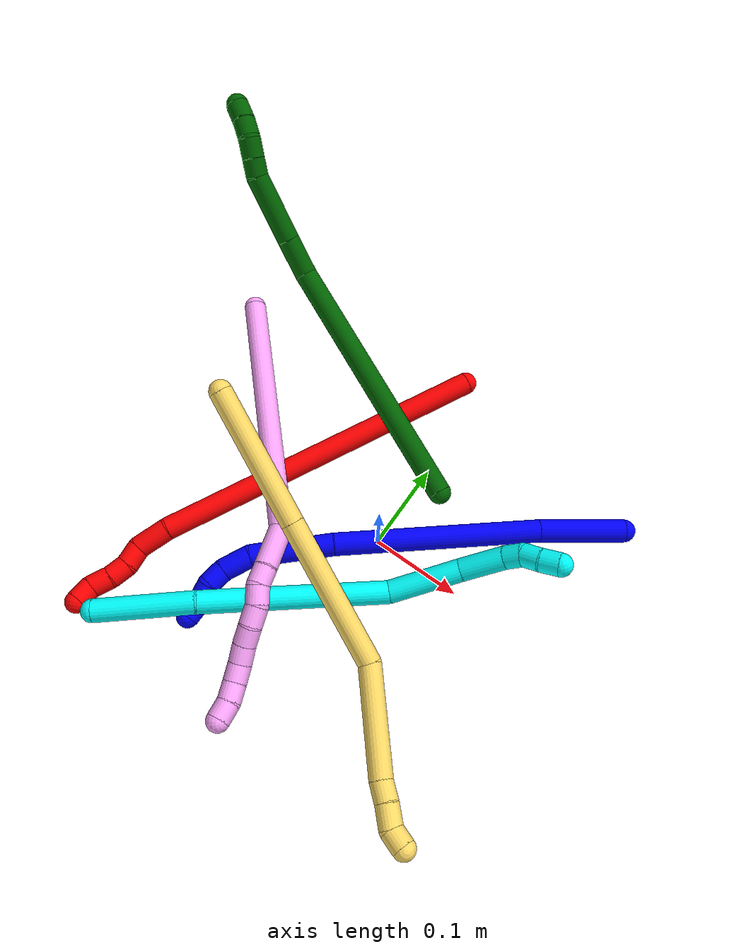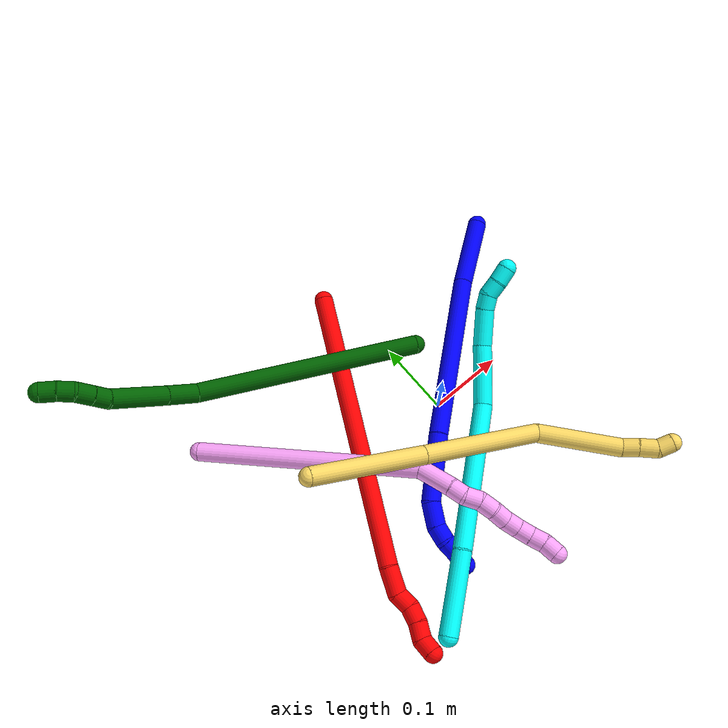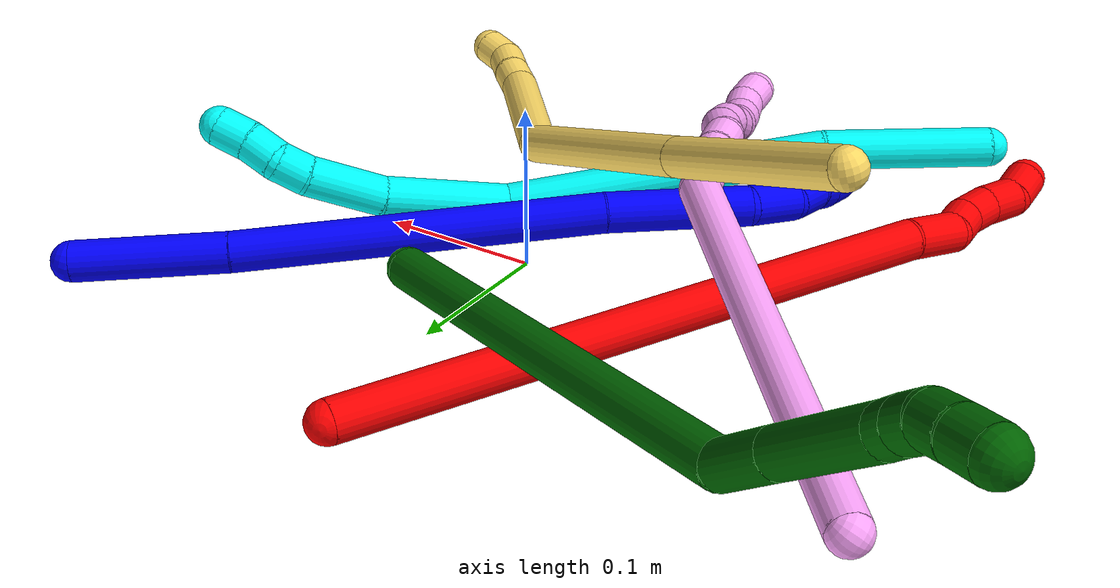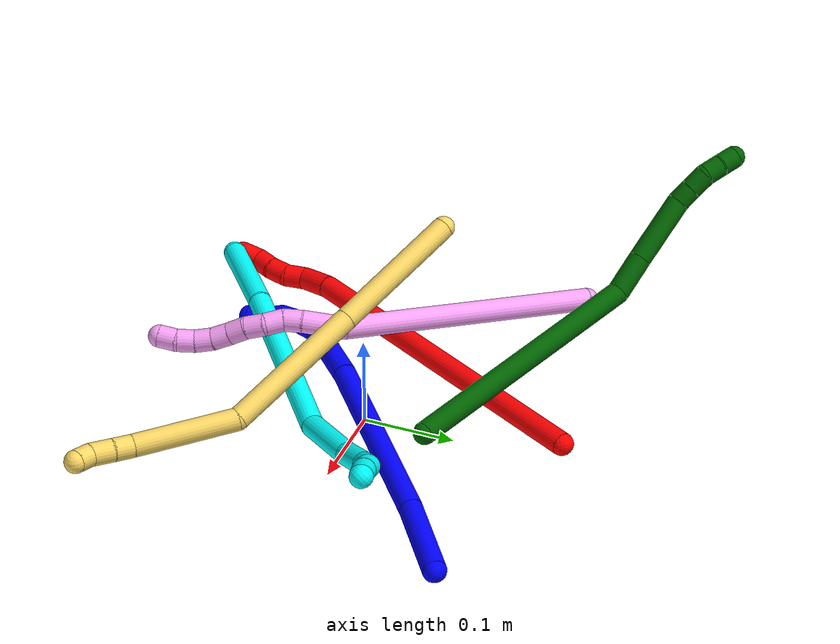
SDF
<sdf version="1.7">
 <world name="default">
  <plugin name="TubeGeneratorPlugin" filename="libtube_generator_plugin.so"/>
  <model name="photoneo_s_sensor">
   <static>1</static>
   <pose>0 0 2 1.57079 1.57079 3.14159</pose>
   <link name="link">
    <inertial><mass>0.1</mass></inertial>
    <sensor name="sensor" type="depth">
     <update_rate>30</update_rate>
     <camera>
      <horizontal_fov>1.22</horizontal_fov>
      <image><width>1920</width><height>1200</height><format>B8G8R8</format></image>
      <clip><near>0.1</near><far>4</far></clip>
      <depth_camera><output>points</output></depth_camera>
     </camera>
     <plugin name="camera_plugin" filename="libgazebo_ros_depth_camera.so">
      <baseline>0.2</baseline>
      <alwaysOn>1</alwaysOn>
      <updateRate>0.0</updateRate>
      <cameraName>camera_ir</cameraName>
      <imageTopicName>/camera/color/image_raw</imageTopicName>
      <cameraInfoTopicName>/camera/color/camera_info</cameraInfoTopicName>
      <depthImageTopicName>/camera/depth/image_raw</depthImageTopicName>
      <depthImageCameraInfoTopicName>/camera/depth/camera_info</depthImageCameraInfoTopicName>
      <pointCloudTopicName>/camera/depth/points</pointCloudTopicName>
      <frameName>fr_optical</frameName>
      <pointCloudCutoff>0.1</pointCloudCutoff>
      <pointCloudCutoffMax>2.0</pointCloudCutoffMax>
      <distortionK1>0</distortionK1>
      <distortionK2>0</distortionK2>
      <distortionK3>0</distortionK3>
      <distortionT1>0</distortionT1>
      <distortionT2>0</distortionT2>
      <CxPrime>0</CxPrime>
      <Cx>0</Cx>
      <Cy>0</Cy>
      <focalLength>0</focalLength>
      <hackBaseline>0</hackBaseline>
     </plugin>
    </sensor>
   </link>
  </model>
  <gravity>0 0 -9.8</gravity>
  <magnetic_field>6e-06 2.3e-05 -4.2e-05</magnetic_field>
  <atmosphere type="adiabatic"/>
  <physics name="default_physics" default="0" type="ode">
   <max_step_size>0.003</max_step_size>
   <real_time_factor>1</real_time_factor>
   <real_time_update_rate>1000</real_time_update_rate>
   <max_contacts>10000</max_contacts>
   <ode>
    <solver>
     <type>quick</type>
     <iters>100</iters>
     <sor>1.3</sor>
     <use_dynamic_moi_rescaling>0</use_dynamic_moi_rescaling>
    </solver>
    <constraints>
     <contact_max_correcting_vel>0</contact_max_correcting_vel>
     <contact_surface_layer>0.001</contact_surface_layer>
     <cfm>0</cfm>
     <erp>0.2</erp>
    </constraints>
   </ode>
  </physics>
  <scene><ambient>0.4 0.4 0.4 1</ambient><background>0.7 0.7 0.7 1</background><shadows>0</shadows></scene>
  <audio><device>default</device></audio>
  <spherical_coordinates>
   <surface_model>EARTH_WGS84</surface_model>
   <latitude_deg>0</latitude_deg>
   <longitude_deg>0</longitude_deg>
   <elevation>0</elevation>
   <heading_deg>0</heading_deg>
  </spherical_coordinates>
  <model name="bin">
   <static>1</static>
   <link name="bottom">
    <collision name="collision-bottom">
     <pose>0 0 -0.01 0 -0 0</pose>
     <geometry><box><size>0.8 0.6 0.02</size></box></geometry>
     <surface>
      <friction><ode><mu>100</mu><mu2>100</mu2></ode></friction>
      <contact><collide_bitmask>65535</collide_bitmask></contact>
     </surface>
    </collision>
   </link>
   <link name="west_wall">
    <collision name="collision-west_wall">
     <pose>-0.41 0 0.1 0 -0 0</pose>
     <geometry><box><size>0.02 0.6 0.2</size></box></geometry>
     <surface>
      <friction><ode><mu>100</mu><mu2>100</mu2></ode></friction>
      <contact><collide_bitmask>65535</collide_bitmask></contact>
     </surface>
    </collision>
   </link>
   <link name="east_wall">
    <collision name="collision-east_wall">
     <pose>0.41 0 0.1 0 -0 0</pose>
     <geometry><box><size>0.02 0.6 0.2</size></box></geometry>
     <surface>
      <friction><ode><mu>100</mu><mu2>100</mu2></ode></friction>
      <contact><collide_bitmask>65535</collide_bitmask></contact>
     </surface>
    </collision>
   </link>
   <link name="south_wall">
    <collision name="collision-south_wall">
     <pose>0 -0.31 0.1 0 -0 0</pose>
     <geometry><box><size>0.8 0.02 0.2</size></box></geometry>
     <surface>
      <friction><ode><mu>100</mu><mu2>100</mu2></ode></friction>
      <contact><collide_bitmask>65535</collide_bitmask></contact>
     </surface>
    </collision>
   </link>
   <link name="north_wall">
    <collision name="collision-north_wall">
     <pose>0 0.31 0.1 0 -0 0</pose>
     <geometry><box><size>0.8 0.02 0.2</size></box></geometry>
     <surface>
      <friction><ode><mu>100</mu><mu2>100</mu2></ode></friction>
      <contact><collide_bitmask>65535</collide_bitmask></contact>
     </surface>
    </collision>
   </link>
  </model>
  <model name="1">
   <static>0</static>
   <link name="1">
    <collision name="collision-cylinder-e_1_1_4">
     <pose>-0.014622 0.002071 -0.04436 -3.09495 -0.31809 2.85275</pose>
     <geometry><cylinder><radius>0.0125</radius><length>0.093507</length></cylinder></geometry>
     <surface>
      <friction><ode><mu>1.16</mu><mu2>1.16</mu2><slip1>0</slip1><slip2>0</slip2></ode></friction>
      <contact><ode><kp>1e+06</kp><kd>1</kd><max_vel>0</max_vel><min_depth>0.001</min_depth></ode></contact>
     </surface>
    </collision>
    <visual name="visual-cylinder-e_1_1_4">
     <pose>-0.014622 0.002071 -0.04436 -3.09495 -0.31809 2.85275</pose>
     <geometry><cylinder><radius>0.0125</radius><length>0.093507</length></cylinder></geometry>
     <material><ambient>0 0 1 1</ambient></material>
    </visual>
    <collision name="collision-cylinder-e_2_4_5">
     <pose>-0.070255 0.004104 -0.192635 3.14123 -0.375887 -3.13969</pose>
     <geometry><cylinder><radius>0.0125</radius><length>0.22343</length></cylinder></geometry>
     <surface>
      <friction><ode><mu>1.16</mu><mu2>1.16</mu2><slip1>0</slip1><slip2>0</slip2></ode></friction>
      <contact><ode><kp>1e+06</kp><kd>1</kd><max_vel>0</max_vel><min_depth>0.001</min_depth></ode></contact>
     </surface>
    </collision>
    <visual name="visual-cylinder-e_2_4_5">
     <pose>-0.070255 0.004104 -0.192635 3.14123 -0.375887 -3.13969</pose>
     <geometry><cylinder><radius>0.0125</radius><length>0.22343</length></cylinder></geometry>
     <material><ambient>0 0 1 1</ambient></material>
    </visual>
    <collision name="collision-cylinder-e_3_5_6">
     <pose>-0.126074 -0.000202 -0.338576 3.04037 -0.337195 -2.56311</pose>
     <geometry><cylinder><radius>0.0125</radius><length>0.089525</length></cylinder></geometry>
     <surface>
      <friction><ode><mu>1.16</mu><mu2>1.16</mu2><slip1>0</slip1><slip2>0</slip2></ode></friction>
      <contact><ode><kp>1e+06</kp><kd>1</kd><max_vel>0</max_vel><min_depth>0.001</min_depth></ode></contact>
     </surface>
    </collision>
    <visual name="visual-cylinder-e_3_5_6">
     <pose>-0.126074 -0.000202 -0.338576 3.04037 -0.337195 -2.56311</pose>
     <geometry><cylinder><radius>0.0125</radius><length>0.089525</length></cylinder></geometry>
     <material><ambient>0 0 1 1</ambient></material>
    </visual>
    <collision name="collision-cylinder-e_4_6_7">
     <pose>-0.147819 -0.010876 -0.39366 2.6856 -0.444931 -1.5454</pose>
     <geometry><cylinder><radius>0.0125</radius><length>0.032228</length></cylinder></geometry>
     <surface>
      <friction><ode><mu>1.16</mu><mu2>1.16</mu2><slip1>0</slip1><slip2>0</slip2></ode></friction>
      <contact><ode><kp>1e+06</kp><kd>1</kd><max_vel>0</max_vel><min_depth>0.001</min_depth></ode></contact>
     </surface>
    </collision>
    <visual name="visual-cylinder-e_4_6_7">
     <pose>-0.147819 -0.010876 -0.39366 2.6856 -0.444931 -1.5454</pose>
     <geometry><cylinder><radius>0.0125</radius><length>0.032228</length></cylinder></geometry>
     <material><ambient>0 0 1 1</ambient></material>
    </visual>
    <collision name="collision-cylinder-e_5_7_8">
     <pose>-0.16109 -0.023187 -0.412748 2.36644 -0.643936 -1.3702</pose>
     <geometry><cylinder><radius>0.0125</radius><length>0.021106</length></cylinder></geometry>
     <surface>
      <friction><ode><mu>1.16</mu><mu2>1.16</mu2><slip1>0</slip1><slip2>0</slip2></ode></friction>
      <contact><ode><kp>1e+06</kp><kd>1</kd><max_vel>0</max_vel><min_depth>0.001</min_depth></ode></contact>
     </surface>
    </collision>
    <visual name="visual-cylinder-e_5_7_8">
     <pose>-0.16109 -0.023187 -0.412748 2.36644 -0.643936 -1.3702</pose>
     <geometry><cylinder><radius>0.0125</radius><length>0.021106</length></cylinder></geometry>
     <material><ambient>0 0 1 1</ambient></material>
    </visual>
    <collision name="collision-cylinder-e_6_8_9">
     <pose>-0.171307 -0.037391 -0.422821 2.02437 -0.398047 -0.624303</pose>
     <geometry><cylinder><radius>0.0125</radius><length>0.020028</length></cylinder></geometry>
     <surface>
      <friction><ode><mu>1.16</mu><mu2>1.16</mu2><slip1>0</slip1><slip2>0</slip2></ode></friction>
      <contact><ode><kp>1e+06</kp><kd>1</kd><max_vel>0</max_vel><min_depth>0.001</min_depth></ode></contact>
     </surface>
    </collision>
    <visual name="visual-cylinder-e_6_8_9">
     <pose>-0.171307 -0.037391 -0.422821 2.02437 -0.398047 -0.624303</pose>
     <geometry><cylinder><radius>0.0125</radius><length>0.020028</length></cylinder></geometry>
     <material><ambient>0 0 1 1</ambient></material>
    </visual>
    <collision name="collision-cylinder-e_7_9_2">
     <pose>-0.180935 -0.052384 -0.431757 2.20165 -0.606042 -1.10353</pose>
     <geometry><cylinder><radius>0.0125</radius><length>0.020176</length></cylinder></geometry>
     <surface>
      <friction><ode><mu>1.16</mu><mu2>1.16</mu2><slip1>0</slip1><slip2>0</slip2></ode></friction>
      <contact><ode><kp>1e+06</kp><kd>1</kd><max_vel>0</max_vel><min_depth>0.001</min_depth></ode></contact>
     </surface>
    </collision>
    <visual name="visual-cylinder-e_7_9_2">
     <pose>-0.180935 -0.052384 -0.431757 2.20165 -0.606042 -1.10353</pose>
     <geometry><cylinder><radius>0.0125</radius><length>0.020176</length></cylinder></geometry>
     <material><ambient>0 0 1 1</ambient></material>
    </visual>
    <collision name="collision-sphere-2">
     <pose>-0.186681 -0.05908 -0.436647 0 -0 0</pose>
     <geometry><sphere><radius>0.0125</radius></sphere></geometry>
     <surface>
      <friction><ode><mu>1.16</mu><mu2>1.16</mu2><slip1>0</slip1><slip2>0</slip2></ode></friction>
      <contact><ode><kp>1e+06</kp><kd>1</kd><max_vel>0</max_vel><min_depth>0.001</min_depth></ode></contact>
     </surface>
    </collision>
    <visual name="visual-sphere-2">
     <pose>-0.186681 -0.05908 -0.436647 0 -0 0</pose>
     <geometry><sphere><radius>0.0125</radius></sphere></geometry>
     <material><ambient>0 0 1 1</ambient></material>
    </visual>
    <collision name="collision-sphere-9">
     <pose>-0.175189 -0.045689 -0.426866 0 -0 0</pose>
     <geometry><sphere><radius>0.0125</radius></sphere></geometry>
     <surface>
      <friction><ode><mu>1.16</mu><mu2>1.16</mu2><slip1>0</slip1><slip2>0</slip2></ode></friction>
      <contact><ode><kp>1e+06</kp><kd>1</kd><max_vel>0</max_vel><min_depth>0.001</min_depth></ode></contact>
     </surface>
    </collision>
    <visual name="visual-sphere-9">
     <pose>-0.175189 -0.045689 -0.426866 0 -0 0</pose>
     <geometry><sphere><radius>0.0125</radius></sphere></geometry>
     <material><ambient>0 0 1 1</ambient></material>
    </visual>
    <collision name="collision-sphere-4">
     <pose>-0.029244 0.004141 -0.088719 0 -0 0</pose>
     <geometry><sphere><radius>0.0125</radius></sphere></geometry>
     <surface>
      <friction><ode><mu>1.16</mu><mu2>1.16</mu2><slip1>0</slip1><slip2>0</slip2></ode></friction>
      <contact><ode><kp>1e+06</kp><kd>1</kd><max_vel>0</max_vel><min_depth>0.001</min_depth></ode></contact>
     </surface>
    </collision>
    <visual name="visual-sphere-4">
     <pose>-0.029244 0.004141 -0.088719 0 -0 0</pose>
     <geometry><sphere><radius>0.0125</radius></sphere></geometry>
     <material><ambient>0 0 1 1</ambient></material>
    </visual>
    <collision name="collision-sphere-1">
     <geometry><sphere><radius>0.0125</radius></sphere></geometry>
     <surface>
      <friction><ode><mu>1.16</mu><mu2>1.16</mu2><slip1>0</slip1><slip2>0</slip2></ode></friction>
      <contact><ode><kp>1e+06</kp><kd>1</kd><max_vel>0</max_vel><min_depth>0.001</min_depth></ode></contact>
     </surface>
    </collision>
    <visual name="visual-sphere-1">
     <geometry><sphere><radius>0.0125</radius></sphere></geometry>
     <material><ambient>0 0 1 1</ambient></material>
    </visual>
    <collision name="collision-sphere-8">
     <pose>-0.167426 -0.029093 -0.418776 0 -0 0</pose>
     <geometry><sphere><radius>0.0125</radius></sphere></geometry>
     <surface>
      <friction><ode><mu>1.16</mu><mu2>1.16</mu2><slip1>0</slip1><slip2>0</slip2></ode></friction>
      <contact><ode><kp>1e+06</kp><kd>1</kd><max_vel>0</max_vel><min_depth>0.001</min_depth></ode></contact>
     </surface>
    </collision>
    <visual name="visual-sphere-8">
     <pose>-0.167426 -0.029093 -0.418776 0 -0 0</pose>
     <geometry><sphere><radius>0.0125</radius></sphere></geometry>
     <material><ambient>0 0 1 1</ambient></material>
    </visual>
    <collision name="collision-sphere-5">
     <pose>-0.111265 0.004066 -0.29655 0 -0 0</pose>
     <geometry><sphere><radius>0.0125</radius></sphere></geometry>
     <surface>
      <friction><ode><mu>1.16</mu><mu2>1.16</mu2><slip1>0</slip1><slip2>0</slip2></ode></friction>
      <contact><ode><kp>1e+06</kp><kd>1</kd><max_vel>0</max_vel><min_depth>0.001</min_depth></ode></contact>
     </surface>
    </collision>
    <visual name="visual-sphere-5">
     <pose>-0.111265 0.004066 -0.29655 0 -0 0</pose>
     <geometry><sphere><radius>0.0125</radius></sphere></geometry>
     <material><ambient>0 0 1 1</ambient></material>
    </visual>
    <collision name="collision-sphere-6">
     <pose>-0.140884 -0.004471 -0.380601 0 -0 0</pose>
     <geometry><sphere><radius>0.0125</radius></sphere></geometry>
     <surface>
      <friction><ode><mu>1.16</mu><mu2>1.16</mu2><slip1>0</slip1><slip2>0</slip2></ode></friction>
      <contact><ode><kp>1e+06</kp><kd>1</kd><max_vel>0</max_vel><min_depth>0.001</min_depth></ode></contact>
     </surface>
    </collision>
    <visual name="visual-sphere-6">
     <pose>-0.140884 -0.004471 -0.380601 0 -0 0</pose>
     <geometry><sphere><radius>0.0125</radius></sphere></geometry>
     <material><ambient>0 0 1 1</ambient></material>
    </visual>
    <collision name="collision-sphere-7">
     <pose>-0.154755 -0.017281 -0.406719 0 -0 0</pose>
     <geometry><sphere><radius>0.0125</radius></sphere></geometry>
     <surface>
      <friction><ode><mu>1.16</mu><mu2>1.16</mu2><slip1>0</slip1><slip2>0</slip2></ode></friction>
      <contact><ode><kp>1e+06</kp><kd>1</kd><max_vel>0</max_vel><min_depth>0.001</min_depth></ode></contact>
     </surface>
    </collision>
    <visual name="visual-sphere-7">
     <pose>-0.154755 -0.017281 -0.406719 0 -0 0</pose>
     <geometry><sphere><radius>0.0125</radius></sphere></geometry>
     <material><ambient>0 0 1 1</ambient></material>
    </visual>
    <inertial>
     <pose>-0.087193 -0.003106 -0.232154 0 -0 0</pose>
     <mass>0.5</mass>
     <inertia>
      <ixx>-0.001022</ixx>
      <ixy>0</ixy>
      <ixz>0</ixz>
      <iyy>0.001036</iyy>
      <iyz>0</iyz>
      <izz>0.000366</izz>
     </inertia>
    </inertial>
   </link>
   <pose>0.21392 0.162451 0.011497 1.22666 0.827073 1.76857</pose>
  </model>
  <model name="2">
   <static>0</static>
   <link name="2">
    <collision name="collision-cylinder-e_1_1_4">
     <pose>-0.056402 -0.132897 0.12073 0.83333 -0.304371 -0.13555</pose>
     <geometry><cylinder><radius>0.0125</radius><length>0.376396</length></cylinder></geometry>
     <surface>
      <friction><ode><mu>1.16</mu><mu2>1.16</mu2><slip1>0</slip1><slip2>0</slip2></ode></friction>
      <contact><ode><kp>1e+06</kp><kd>1</kd><max_vel>0</max_vel><min_depth>0.001</min_depth></ode></contact>
     </surface>
    </collision>
    <visual name="visual-cylinder-e_1_1_4">
     <pose>-0.056402 -0.132897 0.12073 0.83333 -0.304371 -0.13555</pose>
     <geometry><cylinder><radius>0.0125</radius><length>0.376396</length></cylinder></geometry>
     <material><ambient>1 0 0 1</ambient></material>
    </visual>
    <collision name="collision-cylinder-e_2_4_5">
     <pose>-0.115259 -0.278183 0.254721 0.751487 -0.134512 -0.053131</pose>
     <geometry><cylinder><radius>0.0125</radius><length>0.036627</length></cylinder></geometry>
     <surface>
      <friction><ode><mu>1.16</mu><mu2>1.16</mu2><slip1>0</slip1><slip2>0</slip2></ode></friction>
      <contact><ode><kp>1e+06</kp><kd>1</kd><max_vel>0</max_vel><min_depth>0.001</min_depth></ode></contact>
     </surface>
    </collision>
    <visual name="visual-cylinder-e_2_4_5">
     <pose>-0.115259 -0.278183 0.254721 0.751487 -0.134512 -0.053131</pose>
     <geometry><cylinder><radius>0.0125</radius><length>0.036627</length></cylinder></geometry>
     <material><ambient>1 0 0 1</ambient></material>
    </visual>
    <collision name="collision-cylinder-e_3_5_6">
     <pose>-0.120324 -0.293364 0.278457 0.260351 -0.236154 -0.031058</pose>
     <geometry><cylinder><radius>0.0125</radius><length>0.0223</length></cylinder></geometry>
     <surface>
      <friction><ode><mu>1.16</mu><mu2>1.16</mu2><slip1>0</slip1><slip2>0</slip2></ode></friction>
      <contact><ode><kp>1e+06</kp><kd>1</kd><max_vel>0</max_vel><min_depth>0.001</min_depth></ode></contact>
     </surface>
    </collision>
    <visual name="visual-cylinder-e_3_5_6">
     <pose>-0.120324 -0.293364 0.278457 0.260351 -0.236154 -0.031058</pose>
     <geometry><cylinder><radius>0.0125</radius><length>0.0223</length></cylinder></geometry>
     <material><ambient>1 0 0 1</ambient></material>
    </visual>
    <collision name="collision-cylinder-e_4_6_7">
     <pose>-0.126382 -0.301918 0.297202 0.60863 -0.329745 -0.104417</pose>
     <geometry><cylinder><radius>0.0125</radius><length>0.021308</length></cylinder></geometry>
     <surface>
      <friction><ode><mu>1.16</mu><mu2>1.16</mu2><slip1>0</slip1><slip2>0</slip2></ode></friction>
      <contact><ode><kp>1e+06</kp><kd>1</kd><max_vel>0</max_vel><min_depth>0.001</min_depth></ode></contact>
     </surface>
    </collision>
    <visual name="visual-cylinder-e_4_6_7">
     <pose>-0.126382 -0.301918 0.297202 0.60863 -0.329745 -0.104417</pose>
     <geometry><cylinder><radius>0.0125</radius><length>0.021308</length></cylinder></geometry>
     <material><ambient>1 0 0 1</ambient></material>
    </visual>
    <collision name="collision-cylinder-e_5_7_8">
     <pose>-0.133332 -0.315532 0.312689 0.827402 -0.317085 -0.140161</pose>
     <geometry><cylinder><radius>0.0125</radius><length>0.022447</length></cylinder></geometry>
     <surface>
      <friction><ode><mu>1.16</mu><mu2>1.16</mu2><slip1>0</slip1><slip2>0</slip2></ode></friction>
      <contact><ode><kp>1e+06</kp><kd>1</kd><max_vel>0</max_vel><min_depth>0.001</min_depth></ode></contact>
     </surface>
    </collision>
    <visual name="visual-cylinder-e_5_7_8">
     <pose>-0.133332 -0.315532 0.312689 0.827402 -0.317085 -0.140161</pose>
     <geometry><cylinder><radius>0.0125</radius><length>0.022447</length></cylinder></geometry>
     <material><ambient>1 0 0 1</ambient></material>
    </visual>
    <collision name="collision-cylinder-e_6_8_2">
     <pose>-0.141627 -0.326453 0.328682 0.336615 -0.476256 -0.082441</pose>
     <geometry><cylinder><radius>0.0125</radius><length>0.020922</length></cylinder></geometry>
     <surface>
      <friction><ode><mu>1.16</mu><mu2>1.16</mu2><slip1>0</slip1><slip2>0</slip2></ode></friction>
      <contact><ode><kp>1e+06</kp><kd>1</kd><max_vel>0</max_vel><min_depth>0.001</min_depth></ode></contact>
     </surface>
    </collision>
    <visual name="visual-cylinder-e_6_8_2">
     <pose>-0.141627 -0.326453 0.328682 0.336615 -0.476256 -0.082441</pose>
     <geometry><cylinder><radius>0.0125</radius><length>0.020922</length></cylinder></geometry>
     <material><ambient>1 0 0 1</ambient></material>
    </visual>
    <collision name="collision-sphere-2">
     <pose>-0.146423 -0.329524 0.337457 0 -0 0</pose>
     <geometry><sphere><radius>0.0125</radius></sphere></geometry>
     <surface>
      <friction><ode><mu>1.16</mu><mu2>1.16</mu2><slip1>0</slip1><slip2>0</slip2></ode></friction>
      <contact><ode><kp>1e+06</kp><kd>1</kd><max_vel>0</max_vel><min_depth>0.001</min_depth></ode></contact>
     </surface>
    </collision>
    <visual name="visual-sphere-2">
     <pose>-0.146423 -0.329524 0.337457 0 -0 0</pose>
     <geometry><sphere><radius>0.0125</radius></sphere></geometry>
     <material><ambient>1 0 0 1</ambient></material>
    </visual>
    <collision name="collision-sphere-4">
     <pose>-0.112803 -0.265793 0.241461 0 -0 0</pose>
     <geometry><sphere><radius>0.0125</radius></sphere></geometry>
     <surface>
      <friction><ode><mu>1.16</mu><mu2>1.16</mu2><slip1>0</slip1><slip2>0</slip2></ode></friction>
      <contact><ode><kp>1e+06</kp><kd>1</kd><max_vel>0</max_vel><min_depth>0.001</min_depth></ode></contact>
     </surface>
    </collision>
    <visual name="visual-sphere-4">
     <pose>-0.112803 -0.265793 0.241461 0 -0 0</pose>
     <geometry><sphere><radius>0.0125</radius></sphere></geometry>
     <material><ambient>1 0 0 1</ambient></material>
    </visual>
    <collision name="collision-sphere-1">
     <geometry><sphere><radius>0.0125</radius></sphere></geometry>
     <surface>
      <friction><ode><mu>1.16</mu><mu2>1.16</mu2><slip1>0</slip1><slip2>0</slip2></ode></friction>
      <contact><ode><kp>1e+06</kp><kd>1</kd><max_vel>0</max_vel><min_depth>0.001</min_depth></ode></contact>
     </surface>
    </collision>
    <visual name="visual-sphere-1">
     <geometry><sphere><radius>0.0125</radius></sphere></geometry>
     <material><ambient>1 0 0 1</ambient></material>
    </visual>
    <collision name="collision-sphere-8">
     <pose>-0.136831 -0.323382 0.319907 0 -0 0</pose>
     <geometry><sphere><radius>0.0125</radius></sphere></geometry>
     <surface>
      <friction><ode><mu>1.16</mu><mu2>1.16</mu2><slip1>0</slip1><slip2>0</slip2></ode></friction>
      <contact><ode><kp>1e+06</kp><kd>1</kd><max_vel>0</max_vel><min_depth>0.001</min_depth></ode></contact>
     </surface>
    </collision>
    <visual name="visual-sphere-8">
     <pose>-0.136831 -0.323382 0.319907 0 -0 0</pose>
     <geometry><sphere><radius>0.0125</radius></sphere></geometry>
     <material><ambient>1 0 0 1</ambient></material>
    </visual>
    <collision name="collision-sphere-5">
     <pose>-0.117715 -0.290573 0.267981 0 -0 0</pose>
     <geometry><sphere><radius>0.0125</radius></sphere></geometry>
     <surface>
      <friction><ode><mu>1.16</mu><mu2>1.16</mu2><slip1>0</slip1><slip2>0</slip2></ode></friction>
      <contact><ode><kp>1e+06</kp><kd>1</kd><max_vel>0</max_vel><min_depth>0.001</min_depth></ode></contact>
     </surface>
    </collision>
    <visual name="visual-sphere-5">
     <pose>-0.117715 -0.290573 0.267981 0 -0 0</pose>
     <geometry><sphere><radius>0.0125</radius></sphere></geometry>
     <material><ambient>1 0 0 1</ambient></material>
    </visual>
    <collision name="collision-sphere-6">
     <pose>-0.122933 -0.296155 0.288932 0 -0 0</pose>
     <geometry><sphere><radius>0.0125</radius></sphere></geometry>
     <surface>
      <friction><ode><mu>1.16</mu><mu2>1.16</mu2><slip1>0</slip1><slip2>0</slip2></ode></friction>
      <contact><ode><kp>1e+06</kp><kd>1</kd><max_vel>0</max_vel><min_depth>0.001</min_depth></ode></contact>
     </surface>
    </collision>
    <visual name="visual-sphere-6">
     <pose>-0.122933 -0.296155 0.288932 0 -0 0</pose>
     <geometry><sphere><radius>0.0125</radius></sphere></geometry>
     <material><ambient>1 0 0 1</ambient></material>
    </visual>
    <collision name="collision-sphere-7">
     <pose>-0.129832 -0.307681 0.305472 0 -0 0</pose>
     <geometry><sphere><radius>0.0125</radius></sphere></geometry>
     <surface>
      <friction><ode><mu>1.16</mu><mu2>1.16</mu2><slip1>0</slip1><slip2>0</slip2></ode></friction>
      <contact><ode><kp>1e+06</kp><kd>1</kd><max_vel>0</max_vel><min_depth>0.001</min_depth></ode></contact>
     </surface>
    </collision>
    <visual name="visual-sphere-7">
     <pose>-0.129832 -0.307681 0.305472 0 -0 0</pose>
     <geometry><sphere><radius>0.0125</radius></sphere></geometry>
     <material><ambient>1 0 0 1</ambient></material>
    </visual>
    <inertial>
     <pose>-0.073566 -0.174198 0.16242 0 -0 0</pose>
     <mass>0.5</mass>
     <inertia>
      <ixx>0.003639</ixx>
      <ixy>0</ixy>
      <ixz>0</ixz>
      <iyy>0.002513</iyy>
      <iyz>0</iyz>
      <izz>0.004521</izz>
     </inertia>
    </inertial>
   </link>
   <pose>-0.023136 0.212405 0.011497 2.30176 1.28202 1.09878</pose>
  </model>
  <model name="3">
   <static>0</static>
   <link name="3">
    <collision name="collision-cylinder-e_1_1_4">
     <pose>0.051277 0.013138 -0.008999 -2.17132 1.26968 -1.89921</pose>
     <geometry><cylinder><radius>0.0125</radius><length>0.107385</length></cylinder></geometry>
     <surface>
      <friction><ode><mu>1.16</mu><mu2>1.16</mu2><slip1>0</slip1><slip2>0</slip2></ode></friction>
      <contact><ode><kp>1e+06</kp><kd>1</kd><max_vel>0</max_vel><min_depth>0.001</min_depth></ode></contact>
     </surface>
    </collision>
    <visual name="visual-cylinder-e_1_1_4">
     <pose>0.051277 0.013138 -0.008999 -2.17132 1.26968 -1.89921</pose>
     <geometry><cylinder><radius>0.0125</radius><length>0.107385</length></cylinder></geometry>
     <material><ambient>0.003922 1 0.996078 1</ambient></material>
    </visual>
    <collision name="collision-cylinder-e_2_4_5">
     <pose>0.1931 0.063581 -0.04338 -2.16826 1.1085 -1.72701</pose>
     <geometry><cylinder><radius>0.0125</radius><length>0.202332</length></cylinder></geometry>
     <surface>
      <friction><ode><mu>1.16</mu><mu2>1.16</mu2><slip1>0</slip1><slip2>0</slip2></ode></friction>
      <contact><ode><kp>1e+06</kp><kd>1</kd><max_vel>0</max_vel><min_depth>0.001</min_depth></ode></contact>
     </surface>
    </collision>
    <visual name="visual-cylinder-e_2_4_5">
     <pose>0.1931 0.063581 -0.04338 -2.16826 1.1085 -1.72701</pose>
     <geometry><cylinder><radius>0.0125</radius><length>0.202332</length></cylinder></geometry>
     <material><ambient>0.003922 1 0.996078 1</ambient></material>
    </visual>
    <collision name="collision-cylinder-e_3_5_6">
     <pose>0.322819 0.109185 -0.065549 -1.20137 1.34739 -1.00099</pose>
     <geometry><cylinder><radius>0.0125</radius><length>0.080342</length></cylinder></geometry>
     <surface>
      <friction><ode><mu>1.16</mu><mu2>1.16</mu2><slip1>0</slip1><slip2>0</slip2></ode></friction>
      <contact><ode><kp>1e+06</kp><kd>1</kd><max_vel>0</max_vel><min_depth>0.001</min_depth></ode></contact>
     </surface>
    </collision>
    <visual name="visual-cylinder-e_3_5_6">
     <pose>0.322819 0.109185 -0.065549 -1.20137 1.34739 -1.00099</pose>
     <geometry><cylinder><radius>0.0125</radius><length>0.080342</length></cylinder></geometry>
     <material><ambient>0.003922 1 0.996078 1</ambient></material>
    </visual>
    <collision name="collision-cylinder-e_4_6_7">
     <pose>0.386223 0.117853 -0.059065 -0.11235 1.43578 -0.098145</pose>
     <geometry><cylinder><radius>0.0125</radius><length>0.048907</length></cylinder></geometry>
     <surface>
      <friction><ode><mu>1.16</mu><mu2>1.16</mu2><slip1>0</slip1><slip2>0</slip2></ode></friction>
      <contact><ode><kp>1e+06</kp><kd>1</kd><max_vel>0</max_vel><min_depth>0.001</min_depth></ode></contact>
     </surface>
    </collision>
    <visual name="visual-cylinder-e_4_6_7">
     <pose>0.386223 0.117853 -0.059065 -0.11235 1.43578 -0.098145</pose>
     <geometry><cylinder><radius>0.0125</radius><length>0.048907</length></cylinder></geometry>
     <material><ambient>0.003922 1 0.996078 1</ambient></material>
    </visual>
    <collision name="collision-cylinder-e_5_7_8">
     <pose>0.420251 0.116311 -0.05496 1.15916 1.36109 0.974584</pose>
     <geometry><cylinder><radius>0.0125</radius><length>0.020034</length></cylinder></geometry>
     <surface>
      <friction><ode><mu>1.16</mu><mu2>1.16</mu2><slip1>0</slip1><slip2>0</slip2></ode></friction>
      <contact><ode><kp>1e+06</kp><kd>1</kd><max_vel>0</max_vel><min_depth>0.001</min_depth></ode></contact>
     </surface>
    </collision>
    <visual name="visual-cylinder-e_5_7_8">
     <pose>0.420251 0.116311 -0.05496 1.15916 1.36109 0.974584</pose>
     <geometry><cylinder><radius>0.0125</radius><length>0.020034</length></cylinder></geometry>
     <material><ambient>0.003922 1 0.996078 1</ambient></material>
    </visual>
    <collision name="collision-cylinder-e_6_8_9">
     <pose>0.438902 0.11025 -0.056706 2.12718 1.0664 1.63104</pose>
     <geometry><cylinder><radius>0.0125</radius><length>0.020226</length></cylinder></geometry>
     <surface>
      <friction><ode><mu>1.16</mu><mu2>1.16</mu2><slip1>0</slip1><slip2>0</slip2></ode></friction>
      <contact><ode><kp>1e+06</kp><kd>1</kd><max_vel>0</max_vel><min_depth>0.001</min_depth></ode></contact>
     </surface>
    </collision>
    <visual name="visual-cylinder-e_6_8_9">
     <pose>0.438902 0.11025 -0.056706 2.12718 1.0664 1.63104</pose>
     <geometry><cylinder><radius>0.0125</radius><length>0.020226</length></cylinder></geometry>
     <material><ambient>0.003922 1 0.996078 1</ambient></material>
    </visual>
    <collision name="collision-cylinder-e_7_9_2">
     <pose>0.457344 0.103333 -0.062168 2.37629 1.17606 2.05533</pose>
     <geometry><cylinder><radius>0.0125</radius><length>0.020774</length></cylinder></geometry>
     <surface>
      <friction><ode><mu>1.16</mu><mu2>1.16</mu2><slip1>0</slip1><slip2>0</slip2></ode></friction>
      <contact><ode><kp>1e+06</kp><kd>1</kd><max_vel>0</max_vel><min_depth>0.001</min_depth></ode></contact>
     </surface>
    </collision>
    <visual name="visual-cylinder-e_7_9_2">
     <pose>0.457344 0.103333 -0.062168 2.37629 1.17606 2.05533</pose>
     <geometry><cylinder><radius>0.0125</radius><length>0.020774</length></cylinder></geometry>
     <material><ambient>0.003922 1 0.996078 1</ambient></material>
    </visual>
    <collision name="collision-sphere-2">
     <pose>0.466932 0.100565 -0.065049 0 -0 0</pose>
     <geometry><sphere><radius>0.0125</radius></sphere></geometry>
     <surface>
      <friction><ode><mu>1.16</mu><mu2>1.16</mu2><slip1>0</slip1><slip2>0</slip2></ode></friction>
      <contact><ode><kp>1e+06</kp><kd>1</kd><max_vel>0</max_vel><min_depth>0.001</min_depth></ode></contact>
     </surface>
    </collision>
    <visual name="visual-sphere-2">
     <pose>0.466932 0.100565 -0.065049 0 -0 0</pose>
     <geometry><sphere><radius>0.0125</radius></sphere></geometry>
     <material><ambient>0.003922 1 0.996078 1</ambient></material>
    </visual>
    <collision name="collision-sphere-9">
     <pose>0.447756 0.1061 -0.059288 0 -0 0</pose>
     <geometry><sphere><radius>0.0125</radius></sphere></geometry>
     <surface>
      <friction><ode><mu>1.16</mu><mu2>1.16</mu2><slip1>0</slip1><slip2>0</slip2></ode></friction>
      <contact><ode><kp>1e+06</kp><kd>1</kd><max_vel>0</max_vel><min_depth>0.001</min_depth></ode></contact>
     </surface>
    </collision>
    <visual name="visual-sphere-9">
     <pose>0.447756 0.1061 -0.059288 0 -0 0</pose>
     <geometry><sphere><radius>0.0125</radius></sphere></geometry>
     <material><ambient>0.003922 1 0.996078 1</ambient></material>
    </visual>
    <collision name="collision-sphere-4">
     <pose>0.102553 0.026277 -0.017997 0 -0 0</pose>
     <geometry><sphere><radius>0.0125</radius></sphere></geometry>
     <surface>
      <friction><ode><mu>1.16</mu><mu2>1.16</mu2><slip1>0</slip1><slip2>0</slip2></ode></friction>
      <contact><ode><kp>1e+06</kp><kd>1</kd><max_vel>0</max_vel><min_depth>0.001</min_depth></ode></contact>
     </surface>
    </collision>
    <visual name="visual-sphere-4">
     <pose>0.102553 0.026277 -0.017997 0 -0 0</pose>
     <geometry><sphere><radius>0.0125</radius></sphere></geometry>
     <material><ambient>0.003922 1 0.996078 1</ambient></material>
    </visual>
    <collision name="collision-sphere-1">
     <geometry><sphere><radius>0.0125</radius></sphere></geometry>
     <surface>
      <friction><ode><mu>1.16</mu><mu2>1.16</mu2><slip1>0</slip1><slip2>0</slip2></ode></friction>
      <contact><ode><kp>1e+06</kp><kd>1</kd><max_vel>0</max_vel><min_depth>0.001</min_depth></ode></contact>
     </surface>
    </collision>
    <visual name="visual-sphere-1">
     <geometry><sphere><radius>0.0125</radius></sphere></geometry>
     <material><ambient>0.003922 1 0.996078 1</ambient></material>
    </visual>
    <collision name="collision-sphere-8">
     <pose>0.430049 0.1144 -0.054125 0 -0 0</pose>
     <geometry><sphere><radius>0.0125</radius></sphere></geometry>
     <surface>
      <friction><ode><mu>1.16</mu><mu2>1.16</mu2><slip1>0</slip1><slip2>0</slip2></ode></friction>
      <contact><ode><kp>1e+06</kp><kd>1</kd><max_vel>0</max_vel><min_depth>0.001</min_depth></ode></contact>
     </surface>
    </collision>
    <visual name="visual-sphere-8">
     <pose>0.430049 0.1144 -0.054125 0 -0 0</pose>
     <geometry><sphere><radius>0.0125</radius></sphere></geometry>
     <material><ambient>0.003922 1 0.996078 1</ambient></material>
    </visual>
    <collision name="collision-sphere-5">
     <pose>0.283646 0.100885 -0.068763 0 -0 0</pose>
     <geometry><sphere><radius>0.0125</radius></sphere></geometry>
     <surface>
      <friction><ode><mu>1.16</mu><mu2>1.16</mu2><slip1>0</slip1><slip2>0</slip2></ode></friction>
      <contact><ode><kp>1e+06</kp><kd>1</kd><max_vel>0</max_vel><min_depth>0.001</min_depth></ode></contact>
     </surface>
    </collision>
    <visual name="visual-sphere-5">
     <pose>0.283646 0.100885 -0.068763 0 -0 0</pose>
     <geometry><sphere><radius>0.0125</radius></sphere></geometry>
     <material><ambient>0.003922 1 0.996078 1</ambient></material>
    </visual>
    <collision name="collision-sphere-6">
     <pose>0.361992 0.117484 -0.062336 0 -0 0</pose>
     <geometry><sphere><radius>0.0125</radius></sphere></geometry>
     <surface>
      <friction><ode><mu>1.16</mu><mu2>1.16</mu2><slip1>0</slip1><slip2>0</slip2></ode></friction>
      <contact><ode><kp>1e+06</kp><kd>1</kd><max_vel>0</max_vel><min_depth>0.001</min_depth></ode></contact>
     </surface>
    </collision>
    <visual name="visual-sphere-6">
     <pose>0.361992 0.117484 -0.062336 0 -0 0</pose>
     <geometry><sphere><radius>0.0125</radius></sphere></geometry>
     <material><ambient>0.003922 1 0.996078 1</ambient></material>
    </visual>
    <collision name="collision-sphere-7">
     <pose>0.410454 0.118222 -0.055794 0 -0 0</pose>
     <geometry><sphere><radius>0.0125</radius></sphere></geometry>
     <surface>
      <friction><ode><mu>1.16</mu><mu2>1.16</mu2><slip1>0</slip1><slip2>0</slip2></ode></friction>
      <contact><ode><kp>1e+06</kp><kd>1</kd><max_vel>0</max_vel><min_depth>0.001</min_depth></ode></contact>
     </surface>
    </collision>
    <visual name="visual-sphere-7">
     <pose>0.410454 0.118222 -0.055794 0 -0 0</pose>
     <geometry><sphere><radius>0.0125</radius></sphere></geometry>
     <material><ambient>0.003922 1 0.996078 1</ambient></material>
    </visual>
    <inertial>
     <pose>0.232398 0.071036 -0.042876 0 -0 0</pose>
     <mass>0.5</mass>
     <inertia>
      <ixx>-0.00036</ixx>
      <ixy>0</ixy>
      <ixz>0</ixz>
      <iyy>0.000394</iyy>
      <iyz>0</iyz>
      <izz>-0.001086</izz>
     </inertia>
    </inertial>
   </link>
   <pose>-0.193526 -0.238432 0.034596 -0.937981 -0.331363 0.681245</pose>
  </model>
  <model name="4">
   <static>0</static>
   <link name="4">
    <collision name="collision-cylinder-e_1_1_4">
     <pose>0.06498 -0.118577 -0.055182 2.00635 0.461108 0.705476</pose>
     <geometry><cylinder><radius>0.0125</radius><length>0.292082</length></cylinder></geometry>
     <surface>
      <friction><ode><mu>1.16</mu><mu2>1.16</mu2><slip1>0</slip1><slip2>0</slip2></ode></friction>
      <contact><ode><kp>1e+06</kp><kd>1</kd><max_vel>0</max_vel><min_depth>0.001</min_depth></ode></contact>
     </surface>
    </collision>
    <visual name="visual-cylinder-e_1_1_4">
     <pose>0.06498 -0.118577 -0.055182 2.00635 0.461108 0.705476</pose>
     <geometry><cylinder><radius>0.0125</radius><length>0.292082</length></cylinder></geometry>
     <material><ambient>1 0.65098 0.996078 1</ambient></material>
    </visual>
    <collision name="collision-cylinder-e_2_4_5">
     <pose>0.145607 -0.253604 -0.110557 1.58258 0.760386 0.768539</pose>
     <geometry><cylinder><radius>0.0125</radius><length>0.045409</length></cylinder></geometry>
     <surface>
      <friction><ode><mu>1.16</mu><mu2>1.16</mu2><slip1>0</slip1><slip2>0</slip2></ode></friction>
      <contact><ode><kp>1e+06</kp><kd>1</kd><max_vel>0</max_vel><min_depth>0.001</min_depth></ode></contact>
     </surface>
    </collision>
    <visual name="visual-cylinder-e_2_4_5">
     <pose>0.145607 -0.253604 -0.110557 1.58258 0.760386 0.768539</pose>
     <geometry><cylinder><radius>0.0125</radius><length>0.045409</length></cylinder></geometry>
     <material><ambient>1 0.65098 0.996078 1</ambient></material>
    </visual>
    <collision name="collision-cylinder-e_3_5_6">
     <pose>0.167719 -0.277839 -0.109858 1.4566 0.689776 0.620127</pose>
     <geometry><cylinder><radius>0.0125</radius><length>0.020316</length></cylinder></geometry>
     <surface>
      <friction><ode><mu>1.16</mu><mu2>1.16</mu2><slip1>0</slip1><slip2>0</slip2></ode></friction>
      <contact><ode><kp>1e+06</kp><kd>1</kd><max_vel>0</max_vel><min_depth>0.001</min_depth></ode></contact>
     </surface>
    </collision>
    <visual name="visual-cylinder-e_3_5_6">
     <pose>0.167719 -0.277839 -0.109858 1.4566 0.689776 0.620127</pose>
     <geometry><cylinder><radius>0.0125</radius><length>0.020316</length></cylinder></geometry>
     <material><ambient>1 0.65098 0.996078 1</ambient></material>
    </visual>
    <collision name="collision-cylinder-e_4_6_7">
     <pose>0.177905 -0.295301 -0.10988 1.66506 0.36563 0.400907</pose>
     <geometry><cylinder><radius>0.0125</radius><length>0.020818</length></cylinder></geometry>
     <surface>
      <friction><ode><mu>1.16</mu><mu2>1.16</mu2><slip1>0</slip1><slip2>0</slip2></ode></friction>
      <contact><ode><kp>1e+06</kp><kd>1</kd><max_vel>0</max_vel><min_depth>0.001</min_depth></ode></contact>
     </surface>
    </collision>
    <visual name="visual-cylinder-e_4_6_7">
     <pose>0.177905 -0.295301 -0.10988 1.66506 0.36563 0.400907</pose>
     <geometry><cylinder><radius>0.0125</radius><length>0.020818</length></cylinder></geometry>
     <material><ambient>1 0.65098 0.996078 1</ambient></material>
    </visual>
    <collision name="collision-cylinder-e_5_7_8">
     <pose>0.185963 -0.314362 -0.108557 1.33666 0.422489 0.335444</pose>
     <geometry><cylinder><radius>0.0125</radius><length>0.021151</length></cylinder></geometry>
     <surface>
      <friction><ode><mu>1.16</mu><mu2>1.16</mu2><slip1>0</slip1><slip2>0</slip2></ode></friction>
      <contact><ode><kp>1e+06</kp><kd>1</kd><max_vel>0</max_vel><min_depth>0.001</min_depth></ode></contact>
     </surface>
    </collision>
    <visual name="visual-cylinder-e_5_7_8">
     <pose>0.185963 -0.314362 -0.108557 1.33666 0.422489 0.335444</pose>
     <geometry><cylinder><radius>0.0125</radius><length>0.021151</length></cylinder></geometry>
     <material><ambient>1 0.65098 0.996078 1</ambient></material>
    </visual>
    <collision name="collision-cylinder-e_6_8_9">
     <pose>0.192747 -0.332915 -0.102979 1.22144 0.24571 0.172436</pose>
     <geometry><cylinder><radius>0.0125</radius><length>0.020125</length></cylinder></geometry>
     <surface>
      <friction><ode><mu>1.16</mu><mu2>1.16</mu2><slip1>0</slip1><slip2>0</slip2></ode></friction>
      <contact><ode><kp>1e+06</kp><kd>1</kd><max_vel>0</max_vel><min_depth>0.001</min_depth></ode></contact>
     </surface>
    </collision>
    <visual name="visual-cylinder-e_6_8_9">
     <pose>0.192747 -0.332915 -0.102979 1.22144 0.24571 0.172436</pose>
     <geometry><cylinder><radius>0.0125</radius><length>0.020125</length></cylinder></geometry>
     <material><ambient>1 0.65098 0.996078 1</ambient></material>
    </visual>
    <collision name="collision-cylinder-e_7_9_10">
     <pose>0.198024 -0.35145 -0.097555 1.35196 0.286789 0.230578</pose>
     <geometry><cylinder><radius>0.0125</radius><length>0.020003</length></cylinder></geometry>
     <surface>
      <friction><ode><mu>1.16</mu><mu2>1.16</mu2><slip1>0</slip1><slip2>0</slip2></ode></friction>
      <contact><ode><kp>1e+06</kp><kd>1</kd><max_vel>0</max_vel><min_depth>0.001</min_depth></ode></contact>
     </surface>
    </collision>
    <visual name="visual-cylinder-e_7_9_10">
     <pose>0.198024 -0.35145 -0.097555 1.35196 0.286789 0.230578</pose>
     <geometry><cylinder><radius>0.0125</radius><length>0.020003</length></cylinder></geometry>
     <material><ambient>1 0.65098 0.996078 1</ambient></material>
    </visual>
    <collision name="collision-cylinder-e_8_10_11">
     <pose>0.205494 -0.369637 -0.09439 1.44867 0.481237 0.427561</pose>
     <geometry><cylinder><radius>0.0125</radius><length>0.020054</length></cylinder></geometry>
     <surface>
      <friction><ode><mu>1.16</mu><mu2>1.16</mu2><slip1>0</slip1><slip2>0</slip2></ode></friction>
      <contact><ode><kp>1e+06</kp><kd>1</kd><max_vel>0</max_vel><min_depth>0.001</min_depth></ode></contact>
     </surface>
    </collision>
    <visual name="visual-cylinder-e_8_10_11">
     <pose>0.205494 -0.369637 -0.09439 1.44867 0.481237 0.427561</pose>
     <geometry><cylinder><radius>0.0125</radius><length>0.020054</length></cylinder></geometry>
     <material><ambient>1 0.65098 0.996078 1</ambient></material>
    </visual>
    <collision name="collision-cylinder-e_9_11_12">
     <pose>0.216218 -0.386402 -0.093444 1.58799 0.653466 0.663988</pose>
     <geometry><cylinder><radius>0.0125</radius><length>0.020012</length></cylinder></geometry>
     <surface>
      <friction><ode><mu>1.16</mu><mu2>1.16</mu2><slip1>0</slip1><slip2>0</slip2></ode></friction>
      <contact><ode><kp>1e+06</kp><kd>1</kd><max_vel>0</max_vel><min_depth>0.001</min_depth></ode></contact>
     </surface>
    </collision>
    <visual name="visual-cylinder-e_9_11_12">
     <pose>0.216218 -0.386402 -0.093444 1.58799 0.653466 0.663988</pose>
     <geometry><cylinder><radius>0.0125</radius><length>0.020012</length></cylinder></geometry>
     <material><ambient>1 0.65098 0.996078 1</ambient></material>
    </visual>
    <collision name="collision-cylinder-e_10_12_2">
     <pose>0.229648 -0.400954 -0.09195 1.32889 0.823508 0.659167</pose>
     <geometry><cylinder><radius>0.0125</radius><length>0.02003</length></cylinder></geometry>
     <surface>
      <friction><ode><mu>1.16</mu><mu2>1.16</mu2><slip1>0</slip1><slip2>0</slip2></ode></friction>
      <contact><ode><kp>1e+06</kp><kd>1</kd><max_vel>0</max_vel><min_depth>0.001</min_depth></ode></contact>
     </surface>
    </collision>
    <visual name="visual-cylinder-e_10_12_2">
     <pose>0.229648 -0.400954 -0.09195 1.32889 0.823508 0.659167</pose>
     <geometry><cylinder><radius>0.0125</radius><length>0.02003</length></cylinder></geometry>
     <material><ambient>1 0.65098 0.996078 1</ambient></material>
    </visual>
    <collision name="collision-sphere-2">
     <pose>0.236994 -0.407562 -0.090319 0 -0 0</pose>
     <geometry><sphere><radius>0.0125</radius></sphere></geometry>
     <surface>
      <friction><ode><mu>1.16</mu><mu2>1.16</mu2><slip1>0</slip1><slip2>0</slip2></ode></friction>
      <contact><ode><kp>1e+06</kp><kd>1</kd><max_vel>0</max_vel><min_depth>0.001</min_depth></ode></contact>
     </surface>
    </collision>
    <visual name="visual-sphere-2">
     <pose>0.236994 -0.407562 -0.090319 0 -0 0</pose>
     <geometry><sphere><radius>0.0125</radius></sphere></geometry>
     <material><ambient>1 0.65098 0.996078 1</ambient></material>
    </visual>
    <collision name="collision-sphere-12">
     <pose>0.222301 -0.394345 -0.09358 0 -0 0</pose>
     <geometry><sphere><radius>0.0125</radius></sphere></geometry>
     <surface>
      <friction><ode><mu>1.16</mu><mu2>1.16</mu2><slip1>0</slip1><slip2>0</slip2></ode></friction>
      <contact><ode><kp>1e+06</kp><kd>1</kd><max_vel>0</max_vel><min_depth>0.001</min_depth></ode></contact>
     </surface>
    </collision>
    <visual name="visual-sphere-12">
     <pose>0.222301 -0.394345 -0.09358 0 -0 0</pose>
     <geometry><sphere><radius>0.0125</radius></sphere></geometry>
     <material><ambient>1 0.65098 0.996078 1</ambient></material>
    </visual>
    <collision name="collision-sphere-11">
     <pose>0.210135 -0.378459 -0.093307 0 -0 0</pose>
     <geometry><sphere><radius>0.0125</radius></sphere></geometry>
     <surface>
      <friction><ode><mu>1.16</mu><mu2>1.16</mu2><slip1>0</slip1><slip2>0</slip2></ode></friction>
      <contact><ode><kp>1e+06</kp><kd>1</kd><max_vel>0</max_vel><min_depth>0.001</min_depth></ode></contact>
     </surface>
    </collision>
    <visual name="visual-sphere-11">
     <pose>0.210135 -0.378459 -0.093307 0 -0 0</pose>
     <geometry><sphere><radius>0.0125</radius></sphere></geometry>
     <material><ambient>1 0.65098 0.996078 1</ambient></material>
    </visual>
    <collision name="collision-sphere-10">
     <pose>0.200853 -0.360815 -0.095473 0 -0 0</pose>
     <geometry><sphere><radius>0.0125</radius></sphere></geometry>
     <surface>
      <friction><ode><mu>1.16</mu><mu2>1.16</mu2><slip1>0</slip1><slip2>0</slip2></ode></friction>
      <contact><ode><kp>1e+06</kp><kd>1</kd><max_vel>0</max_vel><min_depth>0.001</min_depth></ode></contact>
     </surface>
    </collision>
    <visual name="visual-sphere-10">
     <pose>0.200853 -0.360815 -0.095473 0 -0 0</pose>
     <geometry><sphere><radius>0.0125</radius></sphere></geometry>
     <material><ambient>1 0.65098 0.996078 1</ambient></material>
    </visual>
    <collision name="collision-sphere-9">
     <pose>0.195194 -0.342086 -0.099638 0 -0 0</pose>
     <geometry><sphere><radius>0.0125</radius></sphere></geometry>
     <surface>
      <friction><ode><mu>1.16</mu><mu2>1.16</mu2><slip1>0</slip1><slip2>0</slip2></ode></friction>
      <contact><ode><kp>1e+06</kp><kd>1</kd><max_vel>0</max_vel><min_depth>0.001</min_depth></ode></contact>
     </surface>
    </collision>
    <visual name="visual-sphere-9">
     <pose>0.195194 -0.342086 -0.099638 0 -0 0</pose>
     <geometry><sphere><radius>0.0125</radius></sphere></geometry>
     <material><ambient>1 0.65098 0.996078 1</ambient></material>
    </visual>
    <collision name="collision-sphere-4">
     <pose>0.129959 -0.237155 -0.110364 0 -0 0</pose>
     <geometry><sphere><radius>0.0125</radius></sphere></geometry>
     <surface>
      <friction><ode><mu>1.16</mu><mu2>1.16</mu2><slip1>0</slip1><slip2>0</slip2></ode></friction>
      <contact><ode><kp>1e+06</kp><kd>1</kd><max_vel>0</max_vel><min_depth>0.001</min_depth></ode></contact>
     </surface>
    </collision>
    <visual name="visual-sphere-4">
     <pose>0.129959 -0.237155 -0.110364 0 -0 0</pose>
     <geometry><sphere><radius>0.0125</radius></sphere></geometry>
     <material><ambient>1 0.65098 0.996078 1</ambient></material>
    </visual>
    <collision name="collision-sphere-1">
     <geometry><sphere><radius>0.0125</radius></sphere></geometry>
     <surface>
      <friction><ode><mu>1.16</mu><mu2>1.16</mu2><slip1>0</slip1><slip2>0</slip2></ode></friction>
      <contact><ode><kp>1e+06</kp><kd>1</kd><max_vel>0</max_vel><min_depth>0.001</min_depth></ode></contact>
     </surface>
    </collision>
    <visual name="visual-sphere-1">
     <geometry><sphere><radius>0.0125</radius></sphere></geometry>
     <material><ambient>1 0.65098 0.996078 1</ambient></material>
    </visual>
    <collision name="collision-sphere-8">
     <pose>0.190299 -0.323744 -0.10632 0 -0 0</pose>
     <geometry><sphere><radius>0.0125</radius></sphere></geometry>
     <surface>
      <friction><ode><mu>1.16</mu><mu2>1.16</mu2><slip1>0</slip1><slip2>0</slip2></ode></friction>
      <contact><ode><kp>1e+06</kp><kd>1</kd><max_vel>0</max_vel><min_depth>0.001</min_depth></ode></contact>
     </surface>
    </collision>
    <visual name="visual-sphere-8">
     <pose>0.190299 -0.323744 -0.10632 0 -0 0</pose>
     <geometry><sphere><radius>0.0125</radius></sphere></geometry>
     <material><ambient>1 0.65098 0.996078 1</ambient></material>
    </visual>
    <collision name="collision-sphere-5">
     <pose>0.161255 -0.270054 -0.110751 0 -0 0</pose>
     <geometry><sphere><radius>0.0125</radius></sphere></geometry>
     <surface>
      <friction><ode><mu>1.16</mu><mu2>1.16</mu2><slip1>0</slip1><slip2>0</slip2></ode></friction>
      <contact><ode><kp>1e+06</kp><kd>1</kd><max_vel>0</max_vel><min_depth>0.001</min_depth></ode></contact>
     </surface>
    </collision>
    <visual name="visual-sphere-5">
     <pose>0.161255 -0.270054 -0.110751 0 -0 0</pose>
     <geometry><sphere><radius>0.0125</radius></sphere></geometry>
     <material><ambient>1 0.65098 0.996078 1</ambient></material>
    </visual>
    <collision name="collision-sphere-6">
     <pose>0.174183 -0.285623 -0.108965 0 -0 0</pose>
     <geometry><sphere><radius>0.0125</radius></sphere></geometry>
     <surface>
      <friction><ode><mu>1.16</mu><mu2>1.16</mu2><slip1>0</slip1><slip2>0</slip2></ode></friction>
      <contact><ode><kp>1e+06</kp><kd>1</kd><max_vel>0</max_vel><min_depth>0.001</min_depth></ode></contact>
     </surface>
    </collision>
    <visual name="visual-sphere-6">
     <pose>0.174183 -0.285623 -0.108965 0 -0 0</pose>
     <geometry><sphere><radius>0.0125</radius></sphere></geometry>
     <material><ambient>1 0.65098 0.996078 1</ambient></material>
    </visual>
    <collision name="collision-sphere-7">
     <pose>0.181626 -0.304979 -0.110795 0 -0 0</pose>
     <geometry><sphere><radius>0.0125</radius></sphere></geometry>
     <surface>
      <friction><ode><mu>1.16</mu><mu2>1.16</mu2><slip1>0</slip1><slip2>0</slip2></ode></friction>
      <contact><ode><kp>1e+06</kp><kd>1</kd><max_vel>0</max_vel><min_depth>0.001</min_depth></ode></contact>
     </surface>
    </collision>
    <visual name="visual-sphere-7">
     <pose>0.181626 -0.304979 -0.110795 0 -0 0</pose>
     <geometry><sphere><radius>0.0125</radius></sphere></geometry>
     <material><ambient>1 0.65098 0.996078 1</ambient></material>
    </visual>
    <inertial>
     <pose>0.115047 -0.202996 -0.075164 0 -0 0</pose>
     <mass>0.5</mass>
     <inertia>
      <ixx>0.002678</ixx>
      <ixy>0</ixy>
      <ixz>0</ixz>
      <iyy>0.001074</iyy>
      <iyz>0</iyz>
      <izz>0.000764</izz>
     </inertia>
    </inertial>
   </link>
   <pose>-0.283815 0.151647 0.011499 2.42978 -0.755404 -1.86366</pose>
  </model>
  <model name="5">
   <static>0</static>
   <link name="5">
    <collision name="collision-cylinder-e_1_1_4">
     <pose>0.039719 -0.065608 0.008706 1.43887 0.540522 0.476204</pose>
     <geometry><cylinder><radius>0.0125</radius><length>0.154374</length></cylinder></geometry>
     <surface>
      <friction><ode><mu>1.16</mu><mu2>1.16</mu2><slip1>0</slip1><slip2>0</slip2></ode></friction>
      <contact><ode><kp>1e+06</kp><kd>1</kd><max_vel>0</max_vel><min_depth>0.001</min_depth></ode></contact>
     </surface>
    </collision>
    <visual name="visual-cylinder-e_1_1_4">
     <pose>0.039719 -0.065608 0.008706 1.43887 0.540522 0.476204</pose>
     <geometry><cylinder><radius>0.0125</radius><length>0.154374</length></cylinder></geometry>
     <material><ambient>1 0.858824 0.4 1</ambient></material>
    </visual>
    <collision name="collision-cylinder-e_2_4_5">
     <pose>0.121821 -0.201294 0.025245 1.45948 0.541189 0.486416</pose>
     <geometry><cylinder><radius>0.0125</radius><length>0.164543</length></cylinder></geometry>
     <surface>
      <friction><ode><mu>1.16</mu><mu2>1.16</mu2><slip1>0</slip1><slip2>0</slip2></ode></friction>
      <contact><ode><kp>1e+06</kp><kd>1</kd><max_vel>0</max_vel><min_depth>0.001</min_depth></ode></contact>
     </surface>
    </collision>
    <visual name="visual-cylinder-e_2_4_5">
     <pose>0.121821 -0.201294 0.025245 1.45948 0.541189 0.486416</pose>
     <geometry><cylinder><radius>0.0125</radius><length>0.164543</length></cylinder></geometry>
     <material><ambient>1 0.858824 0.4 1</ambient></material>
    </visual>
    <collision name="collision-cylinder-e_3_5_6">
     <pose>0.212739 -0.301294 0.028961 1.70752 1.01415 1.13463</pose>
     <geometry><cylinder><radius>0.0125</radius><length>0.114332</length></cylinder></geometry>
     <surface>
      <friction><ode><mu>1.16</mu><mu2>1.16</mu2><slip1>0</slip1><slip2>0</slip2></ode></friction>
      <contact><ode><kp>1e+06</kp><kd>1</kd><max_vel>0</max_vel><min_depth>0.001</min_depth></ode></contact>
     </surface>
    </collision>
    <visual name="visual-cylinder-e_3_5_6">
     <pose>0.212739 -0.301294 0.028961 1.70752 1.01415 1.13463</pose>
     <geometry><cylinder><radius>0.0125</radius><length>0.114332</length></cylinder></geometry>
     <material><ambient>1 0.858824 0.4 1</ambient></material>
    </visual>
    <collision name="collision-cylinder-e_4_6_7">
     <pose>0.269601 -0.337724 0.021966 1.98722 0.863526 1.23162</pose>
     <geometry><cylinder><radius>0.0125</radius><length>0.021907</length></cylinder></geometry>
     <surface>
      <friction><ode><mu>1.16</mu><mu2>1.16</mu2><slip1>0</slip1><slip2>0</slip2></ode></friction>
      <contact><ode><kp>1e+06</kp><kd>1</kd><max_vel>0</max_vel><min_depth>0.001</min_depth></ode></contact>
     </surface>
    </collision>
    <visual name="visual-cylinder-e_4_6_7">
     <pose>0.269601 -0.337724 0.021966 1.98722 0.863526 1.23162</pose>
     <geometry><cylinder><radius>0.0125</radius><length>0.021907</length></cylinder></geometry>
     <material><ambient>1 0.858824 0.4 1</ambient></material>
    </visual>
    <collision name="collision-cylinder-e_5_7_8">
     <pose>0.28796 -0.351015 0.016704 1.90863 0.949072 1.25451</pose>
     <geometry><cylinder><radius>0.0125</radius><length>0.024685</length></cylinder></geometry>
     <surface>
      <friction><ode><mu>1.16</mu><mu2>1.16</mu2><slip1>0</slip1><slip2>0</slip2></ode></friction>
      <contact><ode><kp>1e+06</kp><kd>1</kd><max_vel>0</max_vel><min_depth>0.001</min_depth></ode></contact>
     </surface>
    </collision>
    <visual name="visual-cylinder-e_5_7_8">
     <pose>0.28796 -0.351015 0.016704 1.90863 0.949072 1.25451</pose>
     <geometry><cylinder><radius>0.0125</radius><length>0.024685</length></cylinder></geometry>
     <material><ambient>1 0.858824 0.4 1</ambient></material>
    </visual>
    <collision name="collision-cylinder-e_6_8_2">
     <pose>0.302696 -0.365868 0.010534 2.0096 0.485474 0.74327</pose>
     <geometry><cylinder><radius>0.0125</radius><length>0.02016</length></cylinder></geometry>
     <surface>
      <friction><ode><mu>1.16</mu><mu2>1.16</mu2><slip1>0</slip1><slip2>0</slip2></ode></friction>
      <contact><ode><kp>1e+06</kp><kd>1</kd><max_vel>0</max_vel><min_depth>0.001</min_depth></ode></contact>
     </surface>
    </collision>
    <visual name="visual-cylinder-e_6_8_2">
     <pose>0.302696 -0.365868 0.010534 2.0096 0.485474 0.74327</pose>
     <geometry><cylinder><radius>0.0125</radius><length>0.02016</length></cylinder></geometry>
     <material><ambient>1 0.858824 0.4 1</ambient></material>
    </visual>
    <collision name="collision-sphere-2">
     <pose>0.3074 -0.373939 0.006746 0 -0 0</pose>
     <geometry><sphere><radius>0.0125</radius></sphere></geometry>
     <surface>
      <friction><ode><mu>1.16</mu><mu2>1.16</mu2><slip1>0</slip1><slip2>0</slip2></ode></friction>
      <contact><ode><kp>1e+06</kp><kd>1</kd><max_vel>0</max_vel><min_depth>0.001</min_depth></ode></contact>
     </surface>
    </collision>
    <visual name="visual-sphere-2">
     <pose>0.3074 -0.373939 0.006746 0 -0 0</pose>
     <geometry><sphere><radius>0.0125</radius></sphere></geometry>
     <material><ambient>1 0.858824 0.4 1</ambient></material>
    </visual>
    <collision name="collision-sphere-4">
     <pose>0.079438 -0.131216 0.017412 0 -0 0</pose>
     <geometry><sphere><radius>0.0125</radius></sphere></geometry>
     <surface>
      <friction><ode><mu>1.16</mu><mu2>1.16</mu2><slip1>0</slip1><slip2>0</slip2></ode></friction>
      <contact><ode><kp>1e+06</kp><kd>1</kd><max_vel>0</max_vel><min_depth>0.001</min_depth></ode></contact>
     </surface>
    </collision>
    <visual name="visual-sphere-4">
     <pose>0.079438 -0.131216 0.017412 0 -0 0</pose>
     <geometry><sphere><radius>0.0125</radius></sphere></geometry>
     <material><ambient>1 0.858824 0.4 1</ambient></material>
    </visual>
    <collision name="collision-sphere-1">
     <geometry><sphere><radius>0.0125</radius></sphere></geometry>
     <surface>
      <friction><ode><mu>1.16</mu><mu2>1.16</mu2><slip1>0</slip1><slip2>0</slip2></ode></friction>
      <contact><ode><kp>1e+06</kp><kd>1</kd><max_vel>0</max_vel><min_depth>0.001</min_depth></ode></contact>
     </surface>
    </collision>
    <visual name="visual-sphere-1">
     <geometry><sphere><radius>0.0125</radius></sphere></geometry>
     <material><ambient>1 0.858824 0.4 1</ambient></material>
    </visual>
    <collision name="collision-sphere-8">
     <pose>0.297993 -0.357798 0.014321 0 -0 0</pose>
     <geometry><sphere><radius>0.0125</radius></sphere></geometry>
     <surface>
      <friction><ode><mu>1.16</mu><mu2>1.16</mu2><slip1>0</slip1><slip2>0</slip2></ode></friction>
      <contact><ode><kp>1e+06</kp><kd>1</kd><max_vel>0</max_vel><min_depth>0.001</min_depth></ode></contact>
     </surface>
    </collision>
    <visual name="visual-sphere-8">
     <pose>0.297993 -0.357798 0.014321 0 -0 0</pose>
     <geometry><sphere><radius>0.0125</radius></sphere></geometry>
     <material><ambient>1 0.858824 0.4 1</ambient></material>
    </visual>
    <collision name="collision-sphere-5">
     <pose>0.164204 -0.271373 0.033078 0 -0 0</pose>
     <geometry><sphere><radius>0.0125</radius></sphere></geometry>
     <surface>
      <friction><ode><mu>1.16</mu><mu2>1.16</mu2><slip1>0</slip1><slip2>0</slip2></ode></friction>
      <contact><ode><kp>1e+06</kp><kd>1</kd><max_vel>0</max_vel><min_depth>0.001</min_depth></ode></contact>
     </surface>
    </collision>
    <visual name="visual-sphere-5">
     <pose>0.164204 -0.271373 0.033078 0 -0 0</pose>
     <geometry><sphere><radius>0.0125</radius></sphere></geometry>
     <material><ambient>1 0.858824 0.4 1</ambient></material>
    </visual>
    <collision name="collision-sphere-6">
     <pose>0.261275 -0.331215 0.024844 0 -0 0</pose>
     <geometry><sphere><radius>0.0125</radius></sphere></geometry>
     <surface>
      <friction><ode><mu>1.16</mu><mu2>1.16</mu2><slip1>0</slip1><slip2>0</slip2></ode></friction>
      <contact><ode><kp>1e+06</kp><kd>1</kd><max_vel>0</max_vel><min_depth>0.001</min_depth></ode></contact>
     </surface>
    </collision>
    <visual name="visual-sphere-6">
     <pose>0.261275 -0.331215 0.024844 0 -0 0</pose>
     <geometry><sphere><radius>0.0125</radius></sphere></geometry>
     <material><ambient>1 0.858824 0.4 1</ambient></material>
    </visual>
    <collision name="collision-sphere-7">
     <pose>0.277927 -0.344233 0.019087 0 -0 0</pose>
     <geometry><sphere><radius>0.0125</radius></sphere></geometry>
     <surface>
      <friction><ode><mu>1.16</mu><mu2>1.16</mu2><slip1>0</slip1><slip2>0</slip2></ode></friction>
      <contact><ode><kp>1e+06</kp><kd>1</kd><max_vel>0</max_vel><min_depth>0.001</min_depth></ode></contact>
     </surface>
    </collision>
    <visual name="visual-sphere-7">
     <pose>0.277927 -0.344233 0.019087 0 -0 0</pose>
     <geometry><sphere><radius>0.0125</radius></sphere></geometry>
     <material><ambient>1 0.858824 0.4 1</ambient></material>
    </visual>
    <inertial>
     <pose>0.139232 -0.202272 0.01983 0 -0 0</pose>
     <mass>0.5</mass>
     <inertia><ixx>0.000918</ixx><ixy>0</ixy><ixz>0</ixz><iyy>0.00064</iyy><iyz>0</iyz><izz>0.00019</izz></inertia>
    </inertial>
   </link>
   <pose>-0.205904 0.009223 0.120315 2.8695 -0.015748 -1.41294</pose>
  </model>
  <model name="6">
   <static>0</static>
   <link name="6">
    <collision name="collision-cylinder-e_1_1_4">
     <pose>-0.007897 0.007284 0.147816 -0.049235 -0.053308 0.001313</pose>
     <geometry><cylinder><radius>0.0125</radius><length>0.296411</length></cylinder></geometry>
     <surface>
      <friction><ode><mu>1.16</mu><mu2>1.16</mu2><slip1>0</slip1><slip2>0</slip2></ode></friction>
      <contact><ode><kp>1e+06</kp><kd>1</kd><max_vel>0</max_vel><min_depth>0.001</min_depth></ode></contact>
     </surface>
    </collision>
    <visual name="visual-cylinder-e_1_1_4">
     <pose>-0.007897 0.007284 0.147816 -0.049235 -0.053308 0.001313</pose>
     <geometry><cylinder><radius>0.0125</radius><length>0.296411</length></cylinder></geometry>
     <material><ambient>0 0.392157 0.003922 1</ambient></material>
    </visual>
    <collision name="collision-cylinder-e_2_4_5">
     <pose>-0.026764 0.020234 0.314281 -0.295009 -0.512638 0.077844</pose>
     <geometry><cylinder><radius>0.0125</radius><length>0.044734</length></cylinder></geometry>
     <surface>
      <friction><ode><mu>1.16</mu><mu2>1.16</mu2><slip1>0</slip1><slip2>0</slip2></ode></friction>
      <contact><ode><kp>1e+06</kp><kd>1</kd><max_vel>0</max_vel><min_depth>0.001</min_depth></ode></contact>
     </surface>
    </collision>
    <visual name="visual-cylinder-e_2_4_5">
     <pose>-0.026764 0.020234 0.314281 -0.295009 -0.512638 0.077844</pose>
     <geometry><cylinder><radius>0.0125</radius><length>0.044734</length></cylinder></geometry>
     <material><ambient>0 0.392157 0.003922 1</ambient></material>
    </visual>
    <collision name="collision-cylinder-e_3_5_6">
     <pose>-0.056566 0.034932 0.364852 -0.275686 -0.516308 0.073226</pose>
     <geometry><cylinder><radius>0.0125</radius><length>0.076292</length></cylinder></geometry>
     <surface>
      <friction><ode><mu>1.16</mu><mu2>1.16</mu2><slip1>0</slip1><slip2>0</slip2></ode></friction>
      <contact><ode><kp>1e+06</kp><kd>1</kd><max_vel>0</max_vel><min_depth>0.001</min_depth></ode></contact>
     </surface>
    </collision>
    <visual name="visual-cylinder-e_3_5_6">
     <pose>-0.056566 0.034932 0.364852 -0.275686 -0.516308 0.073226</pose>
     <geometry><cylinder><radius>0.0125</radius><length>0.076292</length></cylinder></geometry>
     <material><ambient>0 0.392157 0.003922 1</ambient></material>
    </visual>
    <collision name="collision-cylinder-e_4_6_7">
     <pose>-0.081625 0.044068 0.404602 -0.013536 -0.671909 0.004727</pose>
     <geometry><cylinder><radius>0.0125</radius><length>0.020008</length></cylinder></geometry>
     <surface>
      <friction><ode><mu>1.16</mu><mu2>1.16</mu2><slip1>0</slip1><slip2>0</slip2></ode></friction>
      <contact><ode><kp>1e+06</kp><kd>1</kd><max_vel>0</max_vel><min_depth>0.001</min_depth></ode></contact>
     </surface>
    </collision>
    <visual name="visual-cylinder-e_4_6_7">
     <pose>-0.081625 0.044068 0.404602 -0.013536 -0.671909 0.004727</pose>
     <geometry><cylinder><radius>0.0125</radius><length>0.020008</length></cylinder></geometry>
     <material><ambient>0 0.392157 0.003922 1</ambient></material>
    </visual>
    <collision name="collision-cylinder-e_5_7_8">
     <pose>-0.094409 0.044075 0.421275 0.011204 -0.637882 -0.0037</pose>
     <geometry><cylinder><radius>0.0125</radius><length>0.02202</length></cylinder></geometry>
     <surface>
      <friction><ode><mu>1.16</mu><mu2>1.16</mu2><slip1>0</slip1><slip2>0</slip2></ode></friction>
      <contact><ode><kp>1e+06</kp><kd>1</kd><max_vel>0</max_vel><min_depth>0.001</min_depth></ode></contact>
     </surface>
    </collision>
    <visual name="visual-cylinder-e_5_7_8">
     <pose>-0.094409 0.044075 0.421275 0.011204 -0.637882 -0.0037</pose>
     <geometry><cylinder><radius>0.0125</radius><length>0.02202</length></cylinder></geometry>
     <material><ambient>0 0.392157 0.003922 1</ambient></material>
    </visual>
    <collision name="collision-cylinder-e_6_8_9">
     <pose>-0.10377 0.042974 0.439822 0.102837 -0.279969 -0.014503</pose>
     <geometry><cylinder><radius>0.0125</radius><length>0.020299</length></cylinder></geometry>
     <surface>
      <friction><ode><mu>1.16</mu><mu2>1.16</mu2><slip1>0</slip1><slip2>0</slip2></ode></friction>
      <contact><ode><kp>1e+06</kp><kd>1</kd><max_vel>0</max_vel><min_depth>0.001</min_depth></ode></contact>
     </surface>
    </collision>
    <visual name="visual-cylinder-e_6_8_9">
     <pose>-0.10377 0.042974 0.439822 0.102837 -0.279969 -0.014503</pose>
     <geometry><cylinder><radius>0.0125</radius><length>0.020299</length></cylinder></geometry>
     <material><ambient>0 0.392157 0.003922 1</ambient></material>
    </visual>
    <collision name="collision-cylinder-e_7_9_2">
     <pose>-0.108134 0.041442 0.459508 0.053101 -0.154767 -0.004118</pose>
     <geometry><cylinder><radius>0.0125</radius><length>0.020236</length></cylinder></geometry>
     <surface>
      <friction><ode><mu>1.16</mu><mu2>1.16</mu2><slip1>0</slip1><slip2>0</slip2></ode></friction>
      <contact><ode><kp>1e+06</kp><kd>1</kd><max_vel>0</max_vel><min_depth>0.001</min_depth></ode></contact>
     </surface>
    </collision>
    <visual name="visual-cylinder-e_7_9_2">
     <pose>-0.108134 0.041442 0.459508 0.053101 -0.154767 -0.004118</pose>
     <geometry><cylinder><radius>0.0125</radius><length>0.020236</length></cylinder></geometry>
     <material><ambient>0 0.392157 0.003922 1</ambient></material>
    </visual>
    <collision name="collision-sphere-2">
     <pose>-0.109694 0.040912 0.46949 0 -0 0</pose>
     <geometry><sphere><radius>0.0125</radius></sphere></geometry>
     <surface>
      <friction><ode><mu>1.16</mu><mu2>1.16</mu2><slip1>0</slip1><slip2>0</slip2></ode></friction>
      <contact><ode><kp>1e+06</kp><kd>1</kd><max_vel>0</max_vel><min_depth>0.001</min_depth></ode></contact>
     </surface>
    </collision>
    <visual name="visual-sphere-2">
     <pose>-0.109694 0.040912 0.46949 0 -0 0</pose>
     <geometry><sphere><radius>0.0125</radius></sphere></geometry>
     <material><ambient>0 0.392157 0.003922 1</ambient></material>
    </visual>
    <collision name="collision-sphere-9">
     <pose>-0.106574 0.041973 0.449525 0 -0 0</pose>
     <geometry><sphere><radius>0.0125</radius></sphere></geometry>
     <surface>
      <friction><ode><mu>1.16</mu><mu2>1.16</mu2><slip1>0</slip1><slip2>0</slip2></ode></friction>
      <contact><ode><kp>1e+06</kp><kd>1</kd><max_vel>0</max_vel><min_depth>0.001</min_depth></ode></contact>
     </surface>
    </collision>
    <visual name="visual-sphere-9">
     <pose>-0.106574 0.041973 0.449525 0 -0 0</pose>
     <geometry><sphere><radius>0.0125</radius></sphere></geometry>
     <material><ambient>0 0.392157 0.003922 1</ambient></material>
    </visual>
    <collision name="collision-sphere-4">
     <pose>-0.015794 0.014567 0.295631 0 -0 0</pose>
     <geometry><sphere><radius>0.0125</radius></sphere></geometry>
     <surface>
      <friction><ode><mu>1.16</mu><mu2>1.16</mu2><slip1>0</slip1><slip2>0</slip2></ode></friction>
      <contact><ode><kp>1e+06</kp><kd>1</kd><max_vel>0</max_vel><min_depth>0.001</min_depth></ode></contact>
     </surface>
    </collision>
    <visual name="visual-sphere-4">
     <pose>-0.015794 0.014567 0.295631 0 -0 0</pose>
     <geometry><sphere><radius>0.0125</radius></sphere></geometry>
     <material><ambient>0 0.392157 0.003922 1</ambient></material>
    </visual>
    <collision name="collision-sphere-1">
     <geometry><sphere><radius>0.0125</radius></sphere></geometry>
     <surface>
      <friction><ode><mu>1.16</mu><mu2>1.16</mu2><slip1>0</slip1><slip2>0</slip2></ode></friction>
      <contact><ode><kp>1e+06</kp><kd>1</kd><max_vel>0</max_vel><min_depth>0.001</min_depth></ode></contact>
     </surface>
    </collision>
    <visual name="visual-sphere-1">
     <geometry><sphere><radius>0.0125</radius></sphere></geometry>
     <material><ambient>0 0.392157 0.003922 1</ambient></material>
    </visual>
    <collision name="collision-sphere-8">
     <pose>-0.100965 0.043976 0.430119 0 -0 0</pose>
     <geometry><sphere><radius>0.0125</radius></sphere></geometry>
     <surface>
      <friction><ode><mu>1.16</mu><mu2>1.16</mu2><slip1>0</slip1><slip2>0</slip2></ode></friction>
      <contact><ode><kp>1e+06</kp><kd>1</kd><max_vel>0</max_vel><min_depth>0.001</min_depth></ode></contact>
     </surface>
    </collision>
    <visual name="visual-sphere-8">
     <pose>-0.100965 0.043976 0.430119 0 -0 0</pose>
     <geometry><sphere><radius>0.0125</radius></sphere></geometry>
     <material><ambient>0 0.392157 0.003922 1</ambient></material>
    </visual>
    <collision name="collision-sphere-5">
     <pose>-0.037734 0.025902 0.332931 0 -0 0</pose>
     <geometry><sphere><radius>0.0125</radius></sphere></geometry>
     <surface>
      <friction><ode><mu>1.16</mu><mu2>1.16</mu2><slip1>0</slip1><slip2>0</slip2></ode></friction>
      <contact><ode><kp>1e+06</kp><kd>1</kd><max_vel>0</max_vel><min_depth>0.001</min_depth></ode></contact>
     </surface>
    </collision>
    <visual name="visual-sphere-5">
     <pose>-0.037734 0.025902 0.332931 0 -0 0</pose>
     <geometry><sphere><radius>0.0125</radius></sphere></geometry>
     <material><ambient>0 0.392157 0.003922 1</ambient></material>
    </visual>
    <collision name="collision-sphere-6">
     <pose>-0.075398 0.043962 0.396773 0 -0 0</pose>
     <geometry><sphere><radius>0.0125</radius></sphere></geometry>
     <surface>
      <friction><ode><mu>1.16</mu><mu2>1.16</mu2><slip1>0</slip1><slip2>0</slip2></ode></friction>
      <contact><ode><kp>1e+06</kp><kd>1</kd><max_vel>0</max_vel><min_depth>0.001</min_depth></ode></contact>
     </surface>
    </collision>
    <visual name="visual-sphere-6">
     <pose>-0.075398 0.043962 0.396773 0 -0 0</pose>
     <geometry><sphere><radius>0.0125</radius></sphere></geometry>
     <material><ambient>0 0.392157 0.003922 1</ambient></material>
    </visual>
    <collision name="collision-sphere-7">
     <pose>-0.087853 0.044174 0.412431 0 -0 0</pose>
     <geometry><sphere><radius>0.0125</radius></sphere></geometry>
     <surface>
      <friction><ode><mu>1.16</mu><mu2>1.16</mu2><slip1>0</slip1><slip2>0</slip2></ode></friction>
      <contact><ode><kp>1e+06</kp><kd>1</kd><max_vel>0</max_vel><min_depth>0.001</min_depth></ode></contact>
     </surface>
    </collision>
    <visual name="visual-sphere-7">
     <pose>-0.087853 0.044174 0.412431 0 -0 0</pose>
     <geometry><sphere><radius>0.0125</radius></sphere></geometry>
     <material><ambient>0 0.392157 0.003922 1</ambient></material>
    </visual>
    <inertial>
     <pose>-0.03172 0.018585 0.242614 0 -0 0</pose>
     <mass>0.5</mass>
     <inertia>
      <ixx>0.002224</ixx>
      <ixy>0</ixy>
      <ixz>0</ixz>
      <iyy>0.002242</iyy>
      <iyz>0</iyz>
      <izz>6.1e-05</izz>
     </inertia>
    </inertial>
   </link>
   <pose>0.027508 0.079109 0.024383 1.41551 1.2108 -2.16836</pose>
  </model>
 </world>
</sdf>
